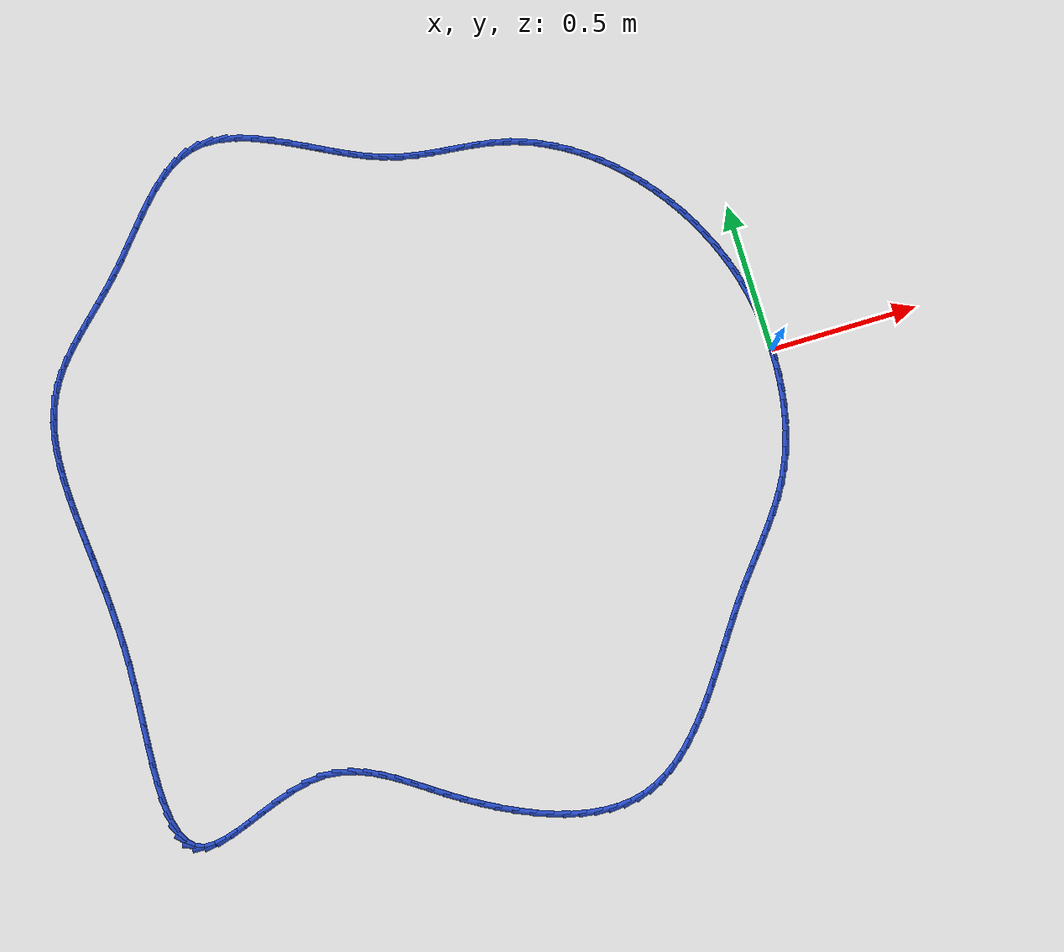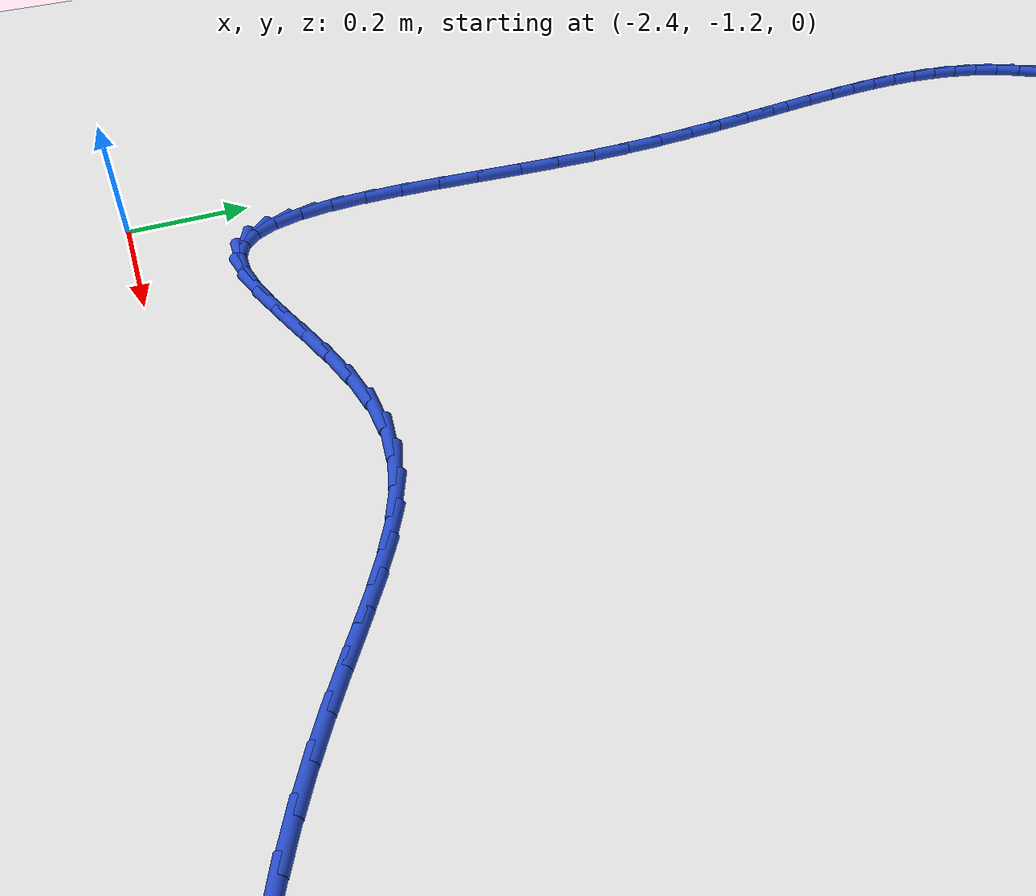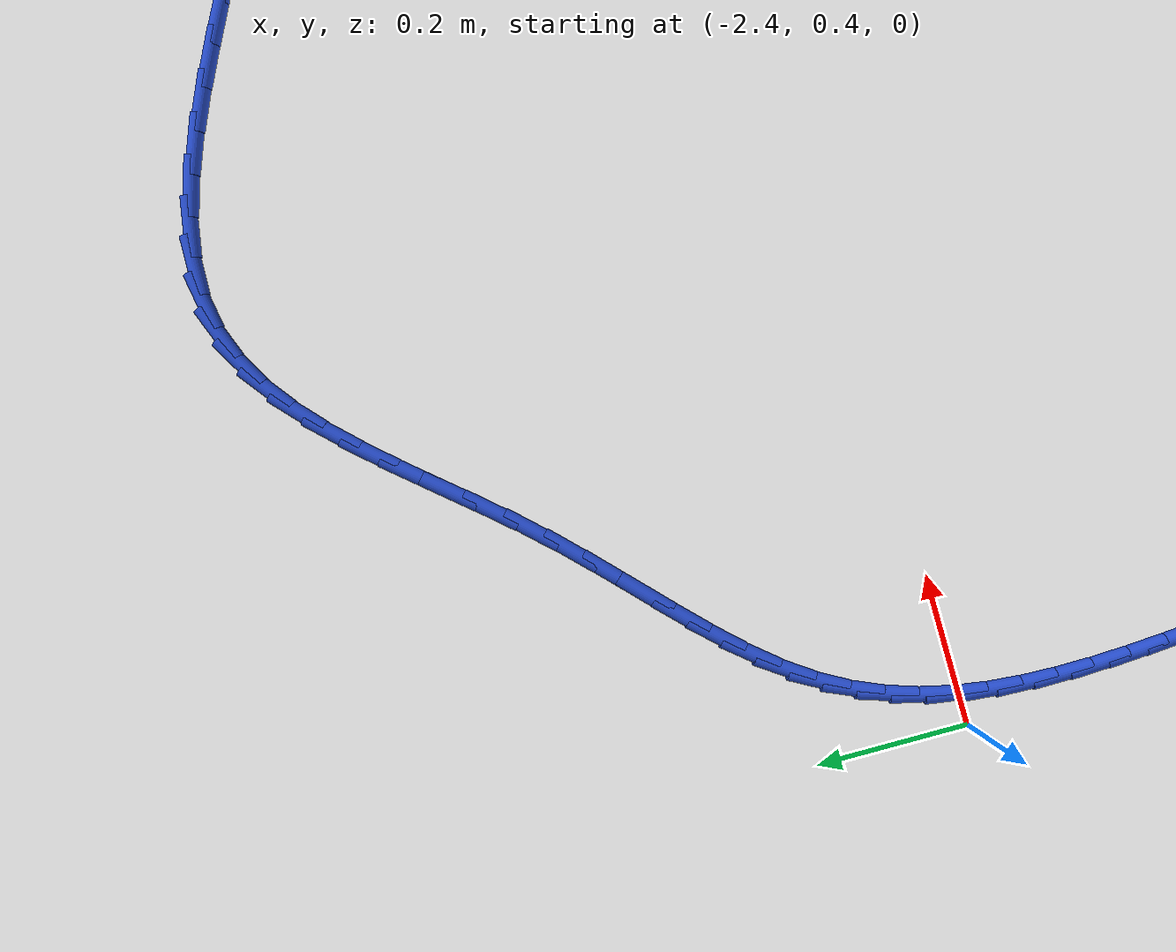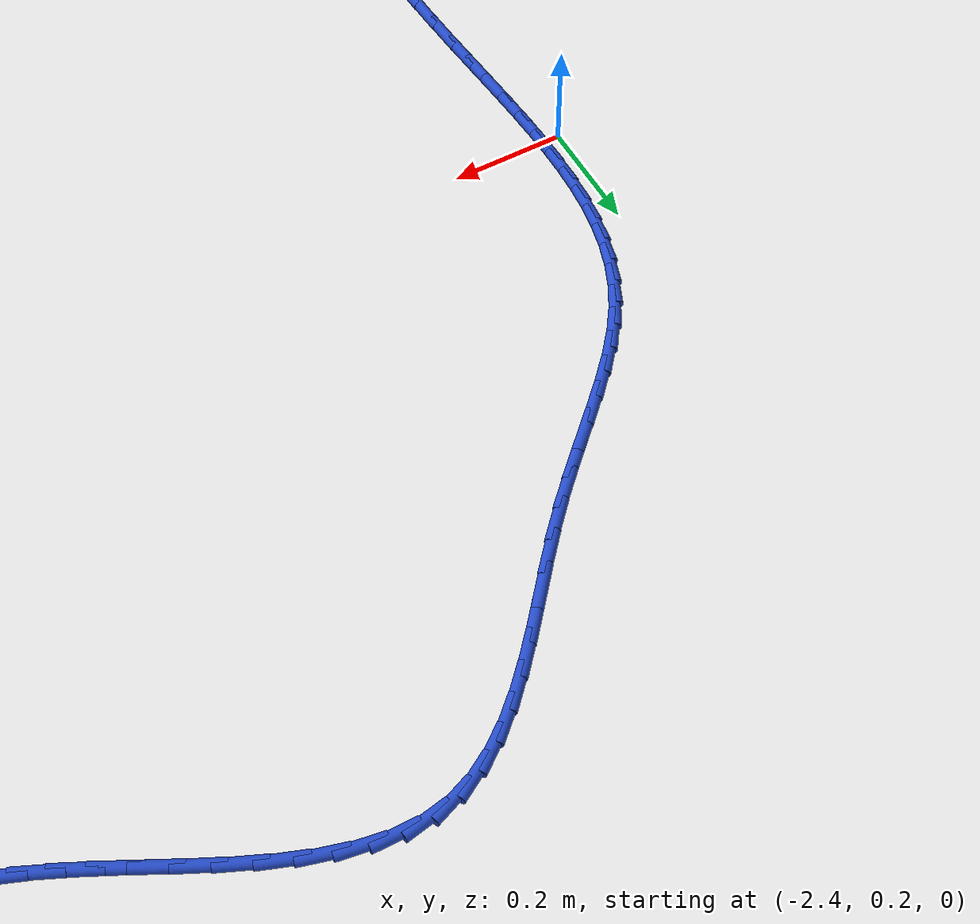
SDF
<sdf version="1.6">
 <world name="default">
  <light name="sun" type="directional">
   <pose>0 0 10 0 -0 0</pose>
   <diffuse>0.8 0.8 0.8 1</diffuse>
   <specular>0.2 0.2 0.2 1</specular>
   <attenuation>
    <range>1000</range>
    <constant>0.9</constant>
    <linear>0.01</linear>
    <quadratic>0.001</quadratic>
   </attenuation>
   <direction>-0.5 0.1 -0.9</direction>
  </light>
  <model name="ground_plane">
   <static>1</static>
   <link name="link">
    <collision name="collision">
     <geometry><plane><normal>0 0 1</normal><size>100 100</size></plane></geometry>
     <surface><friction><ode><mu>100</mu><mu2>50</mu2></ode></friction></surface>
    </collision>
    <visual name="visual">
     <cast_shadows>0</cast_shadows>
     <geometry><plane><normal>0 0 1</normal><size>100 100</size></plane></geometry>
     <material>
      <script><uri>file://media/materials/scripts/gazebo.material</uri><name>Gazebo/WhiteGlow</name></script>
     </material>
    </visual>
   </link>
  </model>
  <gravity>0 0 -9.8</gravity>
  <magnetic_field>6e-06 2.3e-05 -4.2e-05</magnetic_field>
  <atmosphere type="adiabatic"/>
  <physics name="default_physics" default="0" type="ode">
   <max_step_size>0.001</max_step_size>
   <real_time_factor>1</real_time_factor>
   <real_time_update_rate>1000</real_time_update_rate>
  </physics>
  <scene><ambient>0.4 0.4 0.4 1</ambient><background>0.7 0.7 0.7 1</background><shadows>1</shadows></scene>
  <spherical_coordinates>
   <surface_model>EARTH_WGS84</surface_model>
   <latitude_deg>0</latitude_deg>
   <longitude_deg>0</longitude_deg>
   <elevation>0</elevation>
   <heading_deg>0</heading_deg>
  </spherical_coordinates>
  <model name="line">
   <link name="link_0">
    <pose>4.683753385137379e-17 -9.71445146547012e-17 0.01 0 1.57 -1.5415466141234229</pose>
    <collision name="collision">
     <geometry><cylinder><radius>0.01</radius><length>0.08</length></cylinder></geometry>
    </collision>
    <visual name="visual">
     <material>
      <script><name>Gazebo/Blue</name><uri>file://media/materials/scripts/gazebo.material</uri></script>
     </material>
     <geometry><cylinder><radius>0.01</radius><length>0.08</length></cylinder></geometry>
    </visual>
   </link>
   <link name="link_1">
    <pose>-0.0015380150279130165 0.05256723052702508 0.01 0 1.57 -1.4920785525945508</pose>
    <collision name="collision">
     <geometry><cylinder><radius>0.01</radius><length>0.08</length></cylinder></geometry>
    </collision>
    <visual name="visual">
     <material>
      <script><name>Gazebo/Blue</name><uri>file://media/materials/scripts/gazebo.material</uri></script>
     </material>
     <geometry><cylinder><radius>0.01</radius><length>0.08</length></cylinder></geometry>
    </visual>
   </link>
   <link name="link_2">
    <pose>-0.005651078049573215 0.10471001576973192 0.01 0 1.57 -1.4413954976554058</pose>
    <collision name="collision">
     <geometry><cylinder><radius>0.01</radius><length>0.08</length></cylinder></geometry>
    </collision>
    <visual name="visual">
     <material>
      <script><name>Gazebo/Blue</name><uri>file://media/materials/scripts/gazebo.material</uri></script>
     </material>
     <geometry><cylinder><radius>0.01</radius><length>0.08</length></cylinder></geometry>
    </visual>
   </link>
   <link name="link_3">
    <pose>-0.012376972550586392 0.15639679261851733 0.01 0 1.57 -1.3896657407596729</pose>
    <collision name="collision">
     <geometry><cylinder><radius>0.01</radius><length>0.08</length></cylinder></geometry>
    </collision>
    <visual name="visual">
     <material>
      <script><name>Gazebo/Blue</name><uri>file://media/materials/scripts/gazebo.material</uri></script>
     </material>
     <geometry><cylinder><radius>0.01</radius><length>0.08</length></cylinder></geometry>
    </visual>
   </link>
   <link name="link_4">
    <pose>-0.021753482016558384 0.2075959979637782 0.01 0 1.57 -1.337086301904672</pose>
    <collision name="collision">
     <geometry><cylinder><radius>0.01</radius><length>0.08</length></cylinder></geometry>
    </collision>
    <visual name="visual">
     <material>
      <script><name>Gazebo/Blue</name><uri>file://media/materials/scripts/gazebo.material</uri></script>
     </material>
     <geometry><cylinder><radius>0.01</radius><length>0.08</length></cylinder></geometry>
    </visual>
   </link>
   <link name="link_5">
    <pose>-0.03381838993309504 0.2582760686959115 0.01 0 1.57 -1.283879303797767</pose>
    <collision name="collision">
     <geometry><cylinder><radius>0.01</radius><length>0.08</length></cylinder></geometry>
    </collision>
    <visual name="visual">
     <material>
      <script><name>Gazebo/Blue</name><uri>file://media/materials/scripts/gazebo.material</uri></script>
     </material>
     <geometry><cylinder><radius>0.01</radius><length>0.08</length></cylinder></geometry>
    </visual>
   </link>
   <link name="link_6">
    <pose>-0.048609479785802205 0.3084054417053142 0.01 0 1.57 -1.2302867135892297</pose>
    <collision name="collision">
     <geometry><cylinder><radius>0.01</radius><length>0.08</length></cylinder></geometry>
    </collision>
    <visual name="visual">
     <material>
      <script><name>Gazebo/Blue</name><uri>file://media/materials/scripts/gazebo.material</uri></script>
     </material>
     <geometry><cylinder><radius>0.01</radius><length>0.08</length></cylinder></geometry>
    </visual>
   </link>
   <link name="link_7">
    <pose>-0.06616453506028572 0.3579525538823831 0.01 0 1.57 -1.176563697927617</pose>
    <collision name="collision">
     <geometry><cylinder><radius>0.01</radius><length>0.08</length></cylinder></geometry>
    </collision>
    <visual name="visual">
     <material>
      <script><name>Gazebo/Blue</name><uri>file://media/materials/scripts/gazebo.material</uri></script>
     </material>
     <geometry><cylinder><radius>0.01</radius><length>0.08</length></cylinder></geometry>
    </visual>
   </link>
   <link name="link_8">
    <pose>-0.08652133924139689 0.40688584211648177 0.01 0 1.57 -1.123122845600353</pose>
    <collision name="collision">
     <geometry><cylinder><radius>0.01</radius><length>0.08</length></cylinder></geometry>
    </collision>
    <visual name="visual">
     <material>
      <script><name>Gazebo/Blue</name><uri>file://media/materials/scripts/gazebo.material</uri></script>
     </material>
     <geometry><cylinder><radius>0.01</radius><length>0.08</length></cylinder></geometry>
    </visual>
   </link>
   <link name="link_9">
    <pose>-0.10969133001727463 0.4551376683604355 0.01 0 1.57 -1.0705126214260396</pose>
    <collision name="collision">
     <geometry><cylinder><radius>0.01</radius><length>0.08</length></cylinder></geometry>
    </collision>
    <visual name="visual">
     <material>
      <script><name>Gazebo/Blue</name><uri>file://media/materials/scripts/gazebo.material</uri></script>
     </material>
     <geometry><cylinder><radius>0.01</radius><length>0.08</length></cylinder></geometry>
    </visual>
   </link>
   <link name="link_10">
    <pose>-0.13558152764904877 0.5024974172225608 0.01 0 1.57 -1.0183967133618363</pose>
    <collision name="collision">
     <geometry><cylinder><radius>0.01</radius><length>0.08</length></cylinder></geometry>
    </collision>
    <visual name="visual">
     <material>
      <script><name>Gazebo/Blue</name><uri>file://media/materials/scripts/gazebo.material</uri></script>
     </material>
     <geometry><cylinder><radius>0.01</radius><length>0.08</length></cylinder></geometry>
    </visual>
   </link>
   <link name="link_11">
    <pose>-0.16407308727251932 0.5487190565513388 0.01 0 1.57 -0.9662665491765152</pose>
    <collision name="collision">
     <geometry><cylinder><radius>0.01</radius><length>0.08</length></cylinder></geometry>
    </collision>
    <visual name="visual">
     <material>
      <script><name>Gazebo/Blue</name><uri>file://media/materials/scripts/gazebo.material</uri></script>
     </material>
     <geometry><cylinder><radius>0.01</radius><length>0.08</length></cylinder></geometry>
    </visual>
   </link>
   <link name="link_12">
    <pose>-0.19504716402348624 0.5935565541952508 0.01 0 1.57 -0.9136287551357689</pose>
    <collision name="collision">
     <geometry><cylinder><radius>0.01</radius><length>0.08</length></cylinder></geometry>
    </collision>
    <visual name="visual">
     <material>
      <script><name>Gazebo/Blue</name><uri>file://media/materials/scripts/gazebo.material</uri></script>
     </material>
     <geometry><cylinder><radius>0.01</radius><length>0.08</length></cylinder></geometry>
    </visual>
   </link>
   <link name="link_13">
    <pose>-0.22838491303774947 0.6367638780027775 0.01 0 1.57 -0.8599996142701143</pose>
    <collision name="collision">
     <geometry><cylinder><radius>0.01</radius><length>0.08</length></cylinder></geometry>
    </collision>
    <visual name="visual">
     <material>
      <script><name>Gazebo/Blue</name><uri>file://media/materials/scripts/gazebo.material</uri></script>
     </material>
     <geometry><cylinder><radius>0.01</radius><length>0.08</length></cylinder></geometry>
    </visual>
   </link>
   <link name="link_14">
    <pose>-0.2639674894511089 0.6780949958224001 0.01 0 1.57 -0.8049012894406544</pose>
    <collision name="collision">
     <geometry><cylinder><radius>0.01</radius><length>0.08</length></cylinder></geometry>
    </collision>
    <visual name="visual">
     <material>
      <script><name>Gazebo/Blue</name><uri>file://media/materials/scripts/gazebo.material</uri></script>
     </material>
     <geometry><cylinder><radius>0.01</radius><length>0.08</length></cylinder></geometry>
    </visual>
   </link>
   <link name="link_15">
    <pose>-0.3016760483993647 0.7173038755025997 0.01 0 1.57 -0.7478606063406925</pose>
    <collision name="collision">
     <geometry><cylinder><radius>0.01</radius><length>0.08</length></cylinder></geometry>
    </collision>
    <visual name="visual">
     <material>
      <script><name>Gazebo/Blue</name><uri>file://media/materials/scripts/gazebo.material</uri></script>
     </material>
     <geometry><cylinder><radius>0.01</radius><length>0.08</length></cylinder></geometry>
    </visual>
   </link>
   <link name="link_16">
    <pose>-0.34139174501831676 0.7541444848918575 0.01 0 1.57 -0.6884113948911016</pose>
    <collision name="collision">
     <geometry><cylinder><radius>0.01</radius><length>0.08</length></cylinder></geometry>
    </collision>
    <visual name="visual">
     <material>
      <script><name>Gazebo/Blue</name><uri>file://media/materials/scripts/gazebo.material</uri></script>
     </material>
     <geometry><cylinder><radius>0.01</radius><length>0.08</length></cylinder></geometry>
    </visual>
   </link>
   <link name="link_17">
    <pose>-0.38299573444376483 0.7883707918386542 0.01 0 1.57 -0.6261016402470653</pose>
    <collision name="collision">
     <geometry><cylinder><radius>0.01</radius><length>0.08</length></cylinder></geometry>
    </collision>
    <visual name="visual">
     <material>
      <script><name>Gazebo/Blue</name><uri>file://media/materials/scripts/gazebo.material</uri></script>
     </material>
     <geometry><cylinder><radius>0.01</radius><length>0.08</length></cylinder></geometry>
    </visual>
   </link>
   <link name="link_18">
    <pose>-0.4263691718115091 0.819736764191471 0.01 0 1.57 -0.5605069123011129</pose>
    <collision name="collision">
     <geometry><cylinder><radius>0.01</radius><length>0.08</length></cylinder></geometry>
    </collision>
    <visual name="visual">
     <material>
      <script><name>Gazebo/Blue</name><uri>file://media/materials/scripts/gazebo.material</uri></script>
     </material>
     <geometry><cylinder><radius>0.01</radius><length>0.08</length></cylinder></geometry>
    </visual>
   </link>
   <link name="link_19">
    <pose>-0.4713932122573493 0.8479963697987891 0.01 0 1.57 -0.4912515749986578</pose>
    <collision name="collision">
     <geometry><cylinder><radius>0.01</radius><length>0.08</length></cylinder></geometry>
    </collision>
    <visual name="visual">
     <material>
      <script><name>Gazebo/Blue</name><uri>file://media/materials/scripts/gazebo.material</uri></script>
     </material>
     <geometry><cylinder><radius>0.01</radius><length>0.08</length></cylinder></geometry>
    </visual>
   </link>
   <link name="link_20">
    <pose>-0.5179490109170857 0.8729035765090897 0.01 0 1.57 -0.41803888334708594</pose>
    <collision name="collision">
     <geometry><cylinder><radius>0.01</radius><length>0.08</length></cylinder></geometry>
    </collision>
    <visual name="visual">
     <material>
      <script><name>Gazebo/Blue</name><uri>file://media/materials/scripts/gazebo.material</uri></script>
     </material>
     <geometry><cylinder><radius>0.01</radius><length>0.08</length></cylinder></geometry>
    </visual>
   </link>
   <link name="link_21">
    <pose>-0.5659177229265181 0.8942123521708533 0.01 0 1.57 -0.34068993324473923</pose>
    <collision name="collision">
     <geometry><cylinder><radius>0.01</radius><length>0.08</length></cylinder></geometry>
    </collision>
    <visual name="visual">
     <material>
      <script><name>Gazebo/Blue</name><uri>file://media/materials/scripts/gazebo.material</uri></script>
     </material>
     <geometry><cylinder><radius>0.01</radius><length>0.08</length></cylinder></geometry>
    </visual>
   </link>
   <link name="link_22">
    <pose>-0.6151805034214464 0.9116766646325614 0.01 0 1.57 -0.259647384068537</pose>
    <collision name="collision">
     <geometry><cylinder><radius>0.01</radius><length>0.08</length></cylinder></geometry>
    </collision>
    <visual name="visual">
     <material>
      <script><name>Gazebo/Blue</name><uri>file://media/materials/scripts/gazebo.material</uri></script>
     </material>
     <geometry><cylinder><radius>0.01</radius><length>0.08</length></cylinder></geometry>
    </visual>
   </link>
   <link name="link_23">
    <pose>-0.6656144785606424 0.9250741479006304 0.01 0 1.57 -0.18749152417373546</pose>
    <collision name="collision">
     <geometry><cylinder><radius>0.01</radius><length>0.08</length></cylinder></geometry>
    </collision>
    <visual name="visual">
     <material>
      <script><name>Gazebo/Blue</name><uri>file://media/materials/scripts/gazebo.material</uri></script>
     </material>
     <geometry><cylinder><radius>0.01</radius><length>0.08</length></cylinder></geometry>
    </visual>
   </link>
   <link name="link_24">
    <pose>-0.7169881075798372 0.934820744054466 0.01 0 1.57 -0.13781468755106457</pose>
    <collision name="collision">
     <geometry><cylinder><radius>0.01</radius><length>0.08</length></cylinder></geometry>
    </collision>
    <visual name="visual">
     <material>
      <script><name>Gazebo/Blue</name><uri>file://media/materials/scripts/gazebo.material</uri></script>
     </material>
     <geometry><cylinder><radius>0.01</radius><length>0.08</length></cylinder></geometry>
    </visual>
   </link>
   <link name="link_25">
    <pose>-0.7689514720494542 0.9420277440184932 0.01 0 1.57 -0.110924155736938</pose>
    <collision name="collision">
     <geometry><cylinder><radius>0.01</radius><length>0.08</length></cylinder></geometry>
    </collision>
    <visual name="visual">
     <material>
      <script><name>Gazebo/Blue</name><uri>file://media/materials/scripts/gazebo.material</uri></script>
     </material>
     <geometry><cylinder><radius>0.01</radius><length>0.08</length></cylinder></geometry>
    </visual>
   </link>
   <link name="link_26">
    <pose>-0.8211486779530365 0.9478415392356746 0.01 0 1.57 -0.10649837597077871</pose>
    <collision name="collision">
     <geometry><cylinder><radius>0.01</radius><length>0.08</length></cylinder></geometry>
    </collision>
    <visual name="visual">
     <material>
      <script><name>Gazebo/Blue</name><uri>file://media/materials/scripts/gazebo.material</uri></script>
     </material>
     <geometry><cylinder><radius>0.01</radius><length>0.08</length></cylinder></geometry>
    </visual>
   </link>
   <link name="link_27">
    <pose>-0.8732238312741266 0.953408521148972 0.01 0 1.57 -0.12467765539147815</pose>
    <collision name="collision">
     <geometry><cylinder><radius>0.01</radius><length>0.08</length></cylinder></geometry>
    </collision>
    <visual name="visual">
     <material>
      <script><name>Gazebo/Blue</name><uri>file://media/materials/scripts/gazebo.material</uri></script>
     </material>
     <geometry><cylinder><radius>0.01</radius><length>0.08</length></cylinder></geometry>
    </visual>
   </link>
   <link name="link_28">
    <pose>-0.9248210379962669 0.9598750812013485 0.01 0 1.57 -0.16614458556105718</pose>
    <collision name="collision">
     <geometry><cylinder><radius>0.01</radius><length>0.08</length></cylinder></geometry>
    </collision>
    <visual name="visual">
     <material>
      <script><name>Gazebo/Blue</name><uri>file://media/materials/scripts/gazebo.material</uri></script>
     </material>
     <geometry><cylinder><radius>0.01</radius><length>0.08</length></cylinder></geometry>
    </visual>
   </link>
   <link name="link_29">
    <pose>-0.9755844041030004 0.9683876108357663 0.01 0 1.57 -0.23183757921613832</pose>
    <collision name="collision">
     <geometry><cylinder><radius>0.01</radius><length>0.08</length></cylinder></geometry>
    </collision>
    <visual name="visual">
     <material>
      <script><name>Gazebo/Blue</name><uri>file://media/materials/scripts/gazebo.material</uri></script>
     </material>
     <geometry><cylinder><radius>0.01</radius><length>0.08</length></cylinder></geometry>
    </visual>
   </link>
   <link name="link_30">
    <pose>-1.0251587374879436 0.9800912443837164 0.01 0 1.57 -0.312047706217449</pose>
    <collision name="collision">
     <geometry><cylinder><radius>0.01</radius><length>0.08</length></cylinder></geometry>
    </collision>
    <visual name="visual">
     <material>
      <script><name>Gazebo/Blue</name><uri>file://media/materials/scripts/gazebo.material</uri></script>
     </material>
     <geometry><cylinder><radius>0.01</radius><length>0.08</length></cylinder></geometry>
    </visual>
   </link>
   <link name="link_31">
    <pose>-1.073447172660953 0.9956684566922744 0.01 0 1.57 -0.37983506433896475</pose>
    <collision name="collision">
     <geometry><cylinder><radius>0.01</radius><length>0.08</length></cylinder></geometry>
    </collision>
    <visual name="visual">
     <material>
      <script><name>Gazebo/Blue</name><uri>file://media/materials/scripts/gazebo.material</uri></script>
     </material>
     <geometry><cylinder><radius>0.01</radius><length>0.08</length></cylinder></geometry>
    </visual>
   </link>
   <link name="link_32">
    <pose>-1.1209954835743152 1.0146507640374332 0.01 0 1.57 -0.42965821380719876</pose>
    <collision name="collision">
     <geometry><cylinder><radius>0.01</radius><length>0.08</length></cylinder></geometry>
    </collision>
    <visual name="visual">
     <material>
      <script><name>Gazebo/Blue</name><uri>file://media/materials/scripts/gazebo.material</uri></script>
     </material>
     <geometry><cylinder><radius>0.01</radius><length>0.08</length></cylinder></geometry>
    </visual>
   </link>
   <link name="link_33">
    <pose>-1.168447693986961 1.0363937186170487 0.01 0 1.57 -0.46129631175230285</pose>
    <collision name="collision">
     <geometry><cylinder><radius>0.01</radius><length>0.08</length></cylinder></geometry>
    </collision>
    <visual name="visual">
     <material>
      <script><name>Gazebo/Blue</name><uri>file://media/materials/scripts/gazebo.material</uri></script>
     </material>
     <geometry><cylinder><radius>0.01</radius><length>0.08</length></cylinder></geometry>
    </visual>
   </link>
   <link name="link_34">
    <pose>-1.2164478276578201 1.0602528726289766 0.01 0 1.57 -0.47546455752624156</pose>
    <collision name="collision">
     <geometry><cylinder><radius>0.01</radius><length>0.08</length></cylinder></geometry>
    </collision>
    <visual name="visual">
     <material>
      <script><name>Gazebo/Blue</name><uri>file://media/materials/scripts/gazebo.material</uri></script>
     </material>
     <geometry><cylinder><radius>0.01</radius><length>0.08</length></cylinder></geometry>
    </visual>
   </link>
   <link name="link_35">
    <pose>-1.265585394085164 1.0855518241268671 0.01 0 1.57 -0.4727689873372079</pose>
    <collision name="collision">
     <geometry><cylinder><radius>0.01</radius><length>0.08</length></cylinder></geometry>
    </collision>
    <visual name="visual">
     <material>
      <script><name>Gazebo/Blue</name><uri>file://media/materials/scripts/gazebo.material</uri></script>
     </material>
     <geometry><cylinder><radius>0.01</radius><length>0.08</length></cylinder></geometry>
    </visual>
   </link>
   <link name="link_36">
    <pose>-1.3158144010639805 1.1112416647261616 0.01 0 1.57 -0.4535181067150821</pose>
    <collision name="collision">
     <geometry><cylinder><radius>0.01</radius><length>0.08</length></cylinder></geometry>
    </collision>
    <visual name="visual">
     <material>
      <script><name>Gazebo/Blue</name><uri>file://media/materials/scripts/gazebo.material</uri></script>
     </material>
     <geometry><cylinder><radius>0.01</radius><length>0.08</length></cylinder></geometry>
    </visual>
   </link>
   <link name="link_37">
    <pose>-1.3666780116263972 1.136032664784893 0.01 0 1.57 -0.4168555540847507</pose>
    <collision name="collision">
     <geometry><cylinder><radius>0.01</radius><length>0.08</length></cylinder></geometry>
    </collision>
    <visual name="visual">
     <material>
      <script><name>Gazebo/Blue</name><uri>file://media/materials/scripts/gazebo.material</uri></script>
     </material>
     <geometry><cylinder><radius>0.01</radius><length>0.08</length></cylinder></geometry>
    </visual>
   </link>
   <link name="link_38">
    <pose>-1.4177125033881126 1.1586310586971693 0.01 0 1.57 -0.3602195578214304</pose>
    <collision name="collision">
     <geometry><cylinder><radius>0.01</radius><length>0.08</length></cylinder></geometry>
    </collision>
    <visual name="visual">
     <material>
      <script><name>Gazebo/Blue</name><uri>file://media/materials/scripts/gazebo.material</uri></script>
     </material>
     <geometry><cylinder><radius>0.01</radius><length>0.08</length></cylinder></geometry>
    </visual>
   </link>
   <link name="link_39">
    <pose>-1.4684541539648253 1.1777430808570963 0.01 0 1.57 -0.279232193013129</pose>
    <collision name="collision">
     <geometry><cylinder><radius>0.01</radius><length>0.08</length></cylinder></geometry>
    </collision>
    <visual name="visual">
     <material>
      <script><name>Gazebo/Blue</name><uri>file://media/materials/scripts/gazebo.material</uri></script>
     </material>
     <geometry><cylinder><radius>0.01</radius><length>0.08</length></cylinder></geometry>
    </visual>
   </link>
   <link name="link_40">
    <pose>-1.5184392409722343 1.192074965658782 0.01 0 1.57 -0.16775162427579252</pose>
    <collision name="collision">
     <geometry><cylinder><radius>0.01</radius><length>0.08</length></cylinder></geometry>
    </collision>
    <visual name="visual">
     <material>
      <script><name>Gazebo/Blue</name><uri>file://media/materials/scripts/gazebo.material</uri></script>
     </material>
     <geometry><cylinder><radius>0.01</radius><length>0.08</length></cylinder></geometry>
    </visual>
   </link>
   <link name="link_41">
    <pose>-1.567204042026038 1.2003329474963325 0.01 0 1.57 -0.018908075107396106</pose>
    <collision name="collision">
     <geometry><cylinder><radius>0.01</radius><length>0.08</length></cylinder></geometry>
    </collision>
    <visual name="visual">
     <material>
      <script><name>Gazebo/Blue</name><uri>file://media/materials/scripts/gazebo.material</uri></script>
     </material>
     <geometry><cylinder><radius>0.01</radius><length>0.08</length></cylinder></geometry>
    </visual>
   </link>
   <link name="link_42">
    <pose>-1.6142848347419352 1.2012232607638555 0.01 0 1.57 0.1701212312967609</pose>
    <collision name="collision">
     <geometry><cylinder><radius>0.01</radius><length>0.08</length></cylinder></geometry>
    </collision>
    <visual name="visual">
     <material>
      <script><name>Gazebo/Blue</name><uri>file://media/materials/scripts/gazebo.material</uri></script>
     </material>
     <geometry><cylinder><radius>0.01</radius><length>0.08</length></cylinder></geometry>
    </visual>
   </link>
   <link name="link_43">
    <pose>-1.6592343280527753 1.1935017636128293 0.01 0 1.57 0.3661801967702904</pose>
    <collision name="collision">
     <geometry><cylinder><radius>0.01</radius><length>0.08</length></cylinder></geometry>
    </collision>
    <visual name="visual">
     <material>
      <script><name>Gazebo/Blue</name><uri>file://media/materials/scripts/gazebo.material</uri></script>
     </material>
     <geometry><cylinder><radius>0.01</radius><length>0.08</length></cylinder></geometry>
    </visual>
   </link>
   <link name="link_44">
    <pose>-1.7019957820391942 1.1771038066980417 0.01 0 1.57 0.5293730550373316</pose>
    <collision name="collision">
     <geometry><cylinder><radius>0.01</radius><length>0.08</length></cylinder></geometry>
    </collision>
    <visual name="visual">
     <material>
      <script><name>Gazebo/Blue</name><uri>file://media/materials/scripts/gazebo.material</uri></script>
     </material>
     <geometry><cylinder><radius>0.01</radius><length>0.08</length></cylinder></geometry>
    </visual>
   </link>
   <link name="link_45">
    <pose>-1.742910156682548 1.1531658229246404 0.01 0 1.57 0.6550555817626337</pose>
    <collision name="collision">
     <geometry><cylinder><radius>0.01</radius><length>0.08</length></cylinder></geometry>
    </collision>
    <visual name="visual">
     <material>
      <script><name>Gazebo/Blue</name><uri>file://media/materials/scripts/gazebo.material</uri></script>
     </material>
     <geometry><cylinder><radius>0.01</radius><length>0.08</length></cylinder></geometry>
    </visual>
   </link>
   <link name="link_46">
    <pose>-1.782336273179394 1.122878187349913 0.01 0 1.57 0.7467731136661964</pose>
    <collision name="collision">
     <geometry><cylinder><radius>0.01</radius><length>0.08</length></cylinder></geometry>
    </collision>
    <visual name="visual">
     <material>
      <script><name>Gazebo/Blue</name><uri>file://media/materials/scripts/gazebo.material</uri></script>
     </material>
     <geometry><cylinder><radius>0.01</radius><length>0.08</length></cylinder></geometry>
    </visual>
   </link>
   <link name="link_47">
    <pose>-1.8206329527262906 1.0874312750311477 0.01 0 1.57 0.809953976416097</pose>
    <collision name="collision">
     <geometry><cylinder><radius>0.01</radius><length>0.08</length></cylinder></geometry>
    </collision>
    <visual name="visual">
     <material>
      <script><name>Gazebo/Blue</name><uri>file://media/materials/scripts/gazebo.material</uri></script>
     </material>
     <geometry><cylinder><radius>0.01</radius><length>0.08</length></cylinder></geometry>
    </visual>
   </link>
   <link name="link_48">
    <pose>-1.858159016519796 1.0480154610256318 0.01 0 1.57 0.8493652491550342</pose>
    <collision name="collision">
     <geometry><cylinder><radius>0.01</radius><length>0.08</length></cylinder></geometry>
    </collision>
    <visual name="visual">
     <material>
      <script><name>Gazebo/Blue</name><uri>file://media/materials/scripts/gazebo.material</uri></script>
     </material>
     <geometry><cylinder><radius>0.01</radius><length>0.08</length></cylinder></geometry>
    </visual>
   </link>
   <link name="link_49">
    <pose>-1.8952732857564698 1.005821120390654 0.01 0 1.57 0.8683454732291476</pose>
    <collision name="collision">
     <geometry><cylinder><radius>0.01</radius><length>0.08</length></cylinder></geometry>
    </collision>
    <visual name="visual">
     <material>
      <script><name>Gazebo/Blue</name><uri>file://media/materials/scripts/gazebo.material</uri></script>
     </material>
     <geometry><cylinder><radius>0.01</radius><length>0.08</length></cylinder></geometry>
    </visual>
   </link>
   <link name="link_50">
    <pose>-1.9323345816328694 0.9620386281835008 0.01 0 1.57 0.8687525995645669</pose>
    <collision name="collision">
     <geometry><cylinder><radius>0.01</radius><length>0.08</length></cylinder></geometry>
    </collision>
    <visual name="visual">
     <material>
      <script><name>Gazebo/Blue</name><uri>file://media/materials/scripts/gazebo.material</uri></script>
     </material>
     <geometry><cylinder><radius>0.01</radius><length>0.08</length></cylinder></geometry>
    </visual>
   </link>
   <link name="link_51">
    <pose>-1.9697017253455533 0.9178583594614617 0.01 0 1.57 0.8510845574693076</pose>
    <collision name="collision">
     <geometry><cylinder><radius>0.01</radius><length>0.08</length></cylinder></geometry>
    </collision>
    <visual name="visual">
     <material>
      <script><name>Gazebo/Blue</name><uri>file://media/materials/scripts/gazebo.material</uri></script>
     </material>
     <geometry><cylinder><radius>0.01</radius><length>0.08</length></cylinder></geometry>
    </visual>
   </link>
   <link name="link_52">
    <pose>-2.0077335380910797 0.8744706892818236 0.01 0 1.57 0.8164890846452765</pose>
    <collision name="collision">
     <geometry><cylinder><radius>0.01</radius><length>0.08</length></cylinder></geometry>
    </collision>
    <visual name="visual">
     <material>
      <script><name>Gazebo/Blue</name><uri>file://media/materials/scripts/gazebo.material</uri></script>
     </material>
     <geometry><cylinder><radius>0.01</radius><length>0.08</length></cylinder></geometry>
    </visual>
   </link>
   <link name="link_53">
    <pose>-2.0467259559552557 0.8329750158716591 0.01 0 1.57 0.7843755853639921</pose>
    <collision name="collision">
     <geometry><cylinder><radius>0.01</radius><length>0.08</length></cylinder></geometry>
    </collision>
    <visual name="visual">
     <material>
      <script><name>Gazebo/Blue</name><uri>file://media/materials/scripts/gazebo.material</uri></script>
     </material>
     <geometry><cylinder><radius>0.01</radius><length>0.08</length></cylinder></geometry>
    </visual>
   </link>
   <link name="link_54">
    <pose>-2.0862948853971854 0.7934869284267664 0.01 0 1.57 0.7675576930944683</pose>
    <collision name="collision">
     <geometry><cylinder><radius>0.01</radius><length>0.08</length></cylinder></geometry>
    </collision>
    <visual name="visual">
     <material>
      <script><name>Gazebo/Blue</name><uri>file://media/materials/scripts/gazebo.material</uri></script>
     </material>
     <geometry><cylinder><radius>0.01</radius><length>0.08</length></cylinder></geometry>
    </visual>
   </link>
   <link name="link_55">
    <pose>-2.125640570467786 0.7555206711204957 0.01 0 1.57 0.7670903801759016</pose>
    <collision name="collision">
     <geometry><cylinder><radius>0.01</radius><length>0.08</length></cylinder></geometry>
    </collision>
    <visual name="visual">
     <material>
      <script><name>Gazebo/Blue</name><uri>file://media/materials/scripts/gazebo.material</uri></script>
     </material>
     <geometry><cylinder><radius>0.01</radius><length>0.08</length></cylinder></geometry>
    </visual>
   </link>
   <link name="link_56">
    <pose>-2.1639572938121296 0.7185818636712041 0.01 0 1.57 0.7843512614463876</pose>
    <collision name="collision">
     <geometry><cylinder><radius>0.01</radius><length>0.08</length></cylinder></geometry>
    </collision>
    <visual name="visual">
     <material>
      <script><name>Gazebo/Blue</name><uri>file://media/materials/scripts/gazebo.material</uri></script>
     </material>
     <geometry><cylinder><radius>0.01</radius><length>0.08</length></cylinder></geometry>
    </visual>
   </link>
   <link name="link_57">
    <pose>-2.2004393380752885 0.6821761257972505 0.01 0 1.57 0.8213525761232271</pose>
    <collision name="collision">
     <geometry><cylinder><radius>0.01</radius><length>0.08</length></cylinder></geometry>
    </collision>
    <visual name="visual">
     <material>
      <script><name>Gazebo/Blue</name><uri>file://media/materials/scripts/gazebo.material</uri></script>
     </material>
     <geometry><cylinder><radius>0.01</radius><length>0.08</length></cylinder></geometry>
    </visual>
   </link>
   <link name="link_58">
    <pose>-2.234280985902337 0.645809077216992 0.01 0 1.57 0.880725294211941</pose>
    <collision name="collision">
     <geometry><cylinder><radius>0.01</radius><length>0.08</length></cylinder></geometry>
    </collision>
    <visual name="visual">
     <material>
      <script><name>Gazebo/Blue</name><uri>file://media/materials/scripts/gazebo.material</uri></script>
     </material>
     <geometry><cylinder><radius>0.01</radius><length>0.08</length></cylinder></geometry>
    </visual>
   </link>
   <link name="link_59">
    <pose>-2.2646765199383476 0.6089863376487875 0.01 0 1.57 0.9651259260950774</pose>
    <collision name="collision">
     <geometry><cylinder><radius>0.01</radius><length>0.08</length></cylinder></geometry>
    </collision>
    <visual name="visual">
     <material>
      <script><name>Gazebo/Blue</name><uri>file://media/materials/scripts/gazebo.material</uri></script>
     </material>
     <geometry><cylinder><radius>0.01</radius><length>0.08</length></cylinder></geometry>
    </visual>
   </link>
   <link name="link_60">
    <pose>-2.290831020764267 0.5712177623625896 0.01 0 1.57 1.0654334734665476</pose>
    <collision name="collision">
     <geometry><cylinder><radius>0.01</radius><length>0.08</length></cylinder></geometry>
    </collision>
    <visual name="visual">
     <material>
      <script><name>Gazebo/Blue</name><uri>file://media/materials/scripts/gazebo.material</uri></script>
     </material>
     <geometry><cylinder><radius>0.01</radius><length>0.08</length></cylinder></geometry>
    </visual>
   </link>
   <link name="link_61">
    <pose>-2.3124202223223214 0.5321978230789552 0.01 0 1.57 1.1646446879283325</pose>
    <collision name="collision">
     <geometry><cylinder><radius>0.01</radius><length>0.08</length></cylinder></geometry>
    </collision>
    <visual name="visual">
     <material>
      <script><name>Gazebo/Blue</name><uri>file://media/materials/scripts/gazebo.material</uri></script>
     </material>
     <geometry><cylinder><radius>0.01</radius><length>0.08</length></cylinder></geometry>
    </visual>
   </link>
   <link name="link_62">
    <pose>-2.329762436493547 0.49187304635977436 0.01 0 1.57 1.2583311708363665</pose>
    <collision name="collision">
     <geometry><cylinder><radius>0.01</radius><length>0.08</length></cylinder></geometry>
    </collision>
    <visual name="visual">
     <material>
      <script><name>Gazebo/Blue</name><uri>file://media/materials/scripts/gazebo.material</uri></script>
     </material>
     <geometry><cylinder><radius>0.01</radius><length>0.08</length></cylinder></geometry>
    </visual>
   </link>
   <link name="link_63">
    <pose>-2.343222206417527 0.45020809324033517 0.01 0 1.57 1.3437889629129738</pose>
    <collision name="collision">
     <geometry><cylinder><radius>0.01</radius><length>0.08</length></cylinder></geometry>
    </collision>
    <visual name="visual">
     <material>
      <script><name>Gazebo/Blue</name><uri>file://media/materials/scripts/gazebo.material</uri></script>
     </material>
     <geometry><cylinder><radius>0.01</radius><length>0.08</length></cylinder></geometry>
    </visual>
   </link>
   <link name="link_64">
    <pose>-2.3531640752338396 0.4071676247559247 0.01 0 1.57 1.419249392026891</pose>
    <collision name="collision">
     <geometry><cylinder><radius>0.01</radius><length>0.08</length></cylinder></geometry>
    </collision>
    <visual name="visual">
     <material>
      <script><name>Gazebo/Blue</name><uri>file://media/materials/scripts/gazebo.material</uri></script>
     </material>
     <geometry><cylinder><radius>0.01</radius><length>0.08</length></cylinder></geometry>
    </visual>
   </link>
   <link name="link_65">
    <pose>-2.359952586082067 0.3627163019418299 0.01 0 1.57 1.4838718576488055</pose>
    <collision name="collision">
     <geometry><cylinder><radius>0.01</radius><length>0.08</length></cylinder></geometry>
    </collision>
    <visual name="visual">
     <material>
      <script><name>Gazebo/Blue</name><uri>file://media/materials/scripts/gazebo.material</uri></script>
     </material>
     <geometry><cylinder><radius>0.01</radius><length>0.08</length></cylinder></geometry>
    </visual>
   </link>
   <link name="link_66">
    <pose>-2.3639522821017898 0.31681878583333817 0.01 0 1.57 1.5375570756714296</pose>
    <collision name="collision">
     <geometry><cylinder><radius>0.01</radius><length>0.08</length></cylinder></geometry>
    </collision>
    <visual name="visual">
     <material>
      <script><name>Gazebo/Blue</name><uri>file://media/materials/scripts/gazebo.material</uri></script>
     </material>
     <geometry><cylinder><radius>0.01</radius><length>0.08</length></cylinder></geometry>
    </visual>
   </link>
   <link name="link_67">
    <pose>-2.365527706432588 0.26943973746573613 0.01 0 1.57 -1.5608918524345827</pose>
    <collision name="collision">
     <geometry><cylinder><radius>0.01</radius><length>0.08</length></cylinder></geometry>
    </collision>
    <visual name="visual">
     <material>
      <script><name>Gazebo/Blue</name><uri>file://media/materials/scripts/gazebo.material</uri></script>
     </material>
     <geometry><cylinder><radius>0.01</radius><length>0.08</length></cylinder></geometry>
    </visual>
   </link>
   <link name="link_68">
    <pose>-2.3650434022140434 0.22054381787431207 0.01 0 1.57 -1.5276205901495357</pose>
    <collision name="collision">
     <geometry><cylinder><radius>0.01</radius><length>0.08</length></cylinder></geometry>
    </collision>
    <visual name="visual">
     <material>
      <script><name>Gazebo/Blue</name><uri>file://media/materials/scripts/gazebo.material</uri></script>
     </material>
     <geometry><cylinder><radius>0.01</radius><length>0.08</length></cylinder></geometry>
    </visual>
   </link>
   <link name="link_69">
    <pose>-2.3628639125857345 0.17009568809435252 0.01 0 1.57 -1.5034421122580877</pose>
    <collision name="collision">
     <geometry><cylinder><radius>0.01</radius><length>0.08</length></cylinder></geometry>
    </collision>
    <visual name="visual">
     <material>
      <script><name>Gazebo/Blue</name><uri>file://media/materials/scripts/gazebo.material</uri></script>
     </material>
     <geometry><cylinder><radius>0.01</radius><length>0.08</length></cylinder></geometry>
    </visual>
   </link>
   <link name="link_70">
    <pose>-2.3593537806872447 0.11806000916114494 0.01 0 1.57 -1.4875684090410868</pose>
    <collision name="collision">
     <geometry><cylinder><radius>0.01</radius><length>0.08</length></cylinder></geometry>
    </collision>
    <visual name="visual">
     <material>
      <script><name>Gazebo/Blue</name><uri>file://media/materials/scripts/gazebo.material</uri></script>
     </material>
     <geometry><cylinder><radius>0.01</radius><length>0.08</length></cylinder></geometry>
    </visual>
   </link>
   <link name="link_71">
    <pose>-2.354877549658153 0.06440144210997595 0.01 0 1.57 -1.4792581868829755</pose>
    <collision name="collision">
     <geometry><cylinder><radius>0.01</radius><length>0.08</length></cylinder></geometry>
    </collision>
    <visual name="visual">
     <material>
      <script><name>Gazebo/Blue</name><uri>file://media/materials/scripts/gazebo.material</uri></script>
     </material>
     <geometry><cylinder><radius>0.01</radius><length>0.08</length></cylinder></geometry>
    </visual>
   </link>
   <link name="link_72">
    <pose>-2.34979976263804 0.009084647976133689 0.01 0 1.57 -1.477839839660909</pose>
    <collision name="collision">
     <geometry><cylinder><radius>0.01</radius><length>0.08</length></cylinder></geometry>
    </collision>
    <visual name="visual">
     <material>
      <script><name>Gazebo/Blue</name><uri>file://media/materials/scripts/gazebo.material</uri></script>
     </material>
     <geometry><cylinder><radius>0.01</radius><length>0.08</length></cylinder></geometry>
    </visual>
   </link>
   <link name="link_73">
    <pose>-2.3444849627664874 -0.047925712205095033 0.01 0 1.57 -1.4827147392802746</pose>
    <collision name="collision">
     <geometry><cylinder><radius>0.01</radius><length>0.08</length></cylinder></geometry>
    </collision>
    <visual name="visual">
     <material>
      <script><name>Gazebo/Blue</name><uri>file://media/materials/scripts/gazebo.material</uri></script>
     </material>
     <geometry><cylinder><radius>0.01</radius><length>0.08</length></cylinder></geometry>
    </visual>
   </link>
   <link name="link_74">
    <pose>-2.3392976931830742 -0.10666497739842304 0.01 0 1.57 -1.4933494946444272</pose>
    <collision name="collision">
     <geometry><cylinder><radius>0.01</radius><length>0.08</length></cylinder></geometry>
    </collision>
    <visual name="visual">
     <material>
      <script><name>Gazebo/Blue</name><uri>file://media/materials/scripts/gazebo.material</uri></script>
     </material>
     <geometry><cylinder><radius>0.01</radius><length>0.08</length></cylinder></geometry>
    </visual>
   </link>
   <link name="link_75">
    <pose>-2.334602497027382 -0.16716848656856312 0.01 0 1.57 -1.5092627261936897</pose>
    <collision name="collision">
     <geometry><cylinder><radius>0.01</radius><length>0.08</length></cylinder></geometry>
    </collision>
    <visual name="visual">
     <material>
      <script><name>Gazebo/Blue</name><uri>file://media/materials/scripts/gazebo.material</uri></script>
     </material>
     <geometry><cylinder><radius>0.01</radius><length>0.08</length></cylinder></geometry>
    </visual>
   </link>
   <link name="link_76">
    <pose>-2.330763917438993 -0.22947157868022855 0.01 0 1.57 -1.530009776665142</pose>
    <collision name="collision">
     <geometry><cylinder><radius>0.01</radius><length>0.08</length></cylinder></geometry>
    </collision>
    <visual name="visual">
     <material>
      <script><name>Gazebo/Blue</name><uri>file://media/materials/scripts/gazebo.material</uri></script>
     </material>
     <geometry><cylinder><radius>0.01</radius><length>0.08</length></cylinder></geometry>
    </visual>
   </link>
   <link name="link_77">
    <pose>-2.3281464975574853 -0.29360959269813164 0.01 0 1.57 -1.5551674827939042</pose>
    <collision name="collision">
     <geometry><cylinder><radius>0.01</radius><length>0.08</length></cylinder></geometry>
    </collision>
    <visual name="visual">
     <material>
      <script><name>Gazebo/Blue</name><uri>file://media/materials/scripts/gazebo.material</uri></script>
     </material>
     <geometry><cylinder><radius>0.01</radius><length>0.08</length></cylinder></geometry>
    </visual>
   </link>
   <link name="link_78">
    <pose>-2.327114780522441 -0.3596178675869841 0.01 0 1.57 1.55745078624713</pose>
    <collision name="collision">
     <geometry><cylinder><radius>0.01</radius><length>0.08</length></cylinder></geometry>
    </collision>
    <visual name="visual">
     <material>
      <script><name>Gazebo/Blue</name><uri>file://media/materials/scripts/gazebo.material</uri></script>
     </material>
     <geometry><cylinder><radius>0.01</radius><length>0.08</length></cylinder></geometry>
    </visual>
   </link>
   <link name="link_79">
    <pose>-2.328021019264337 -0.4275195712757638 0.01 0 1.57 1.5316532512382517</pose>
    <collision name="collision">
     <geometry><cylinder><radius>0.01</radius><length>0.08</length></cylinder></geometry>
    </collision>
    <visual name="visual">
     <material>
      <script><name>Gazebo/Blue</name><uri>file://media/materials/scripts/gazebo.material</uri></script>
     </material>
     <geometry><cylinder><radius>0.01</radius><length>0.08</length></cylinder></geometry>
    </visual>
   </link>
   <link name="link_80">
    <pose>-2.3307366720785 -0.49686173913643933 0.01 0 1.57 1.5167643529252266</pose>
    <collision name="collision">
     <geometry><cylinder><radius>0.01</radius><length>0.08</length></cylinder></geometry>
    </collision>
    <visual name="visual">
     <material>
      <script><name>Gazebo/Blue</name><uri>file://media/materials/scripts/gazebo.material</uri></script>
     </material>
     <geometry><cylinder><radius>0.01</radius><length>0.08</length></cylinder></geometry>
    </visual>
   </link>
   <link name="link_81">
    <pose>-2.33450687948605 -0.5665711619260696 0.01 0 1.57 1.5124554049348993</pose>
    <collision name="collision">
     <geometry><cylinder><radius>0.01</radius><length>0.08</length></cylinder></geometry>
    </collision>
    <visual name="visual">
     <material>
      <script><name>Gazebo/Blue</name><uri>file://media/materials/scripts/gazebo.material</uri></script>
     </material>
     <geometry><cylinder><radius>0.01</radius><length>0.08</length></cylinder></geometry>
    </visual>
   </link>
   <link name="link_82">
    <pose>-2.338534747785223 -0.6355330037683017 0.01 0 1.57 1.518851066210437</pose>
    <collision name="collision">
     <geometry><cylinder><radius>0.01</radius><length>0.08</length></cylinder></geometry>
    </collision>
    <visual name="visual">
     <material>
      <script><name>Gazebo/Blue</name><uri>file://media/materials/scripts/gazebo.material</uri></script>
     </material>
     <geometry><cylinder><radius>0.01</radius><length>0.08</length></cylinder></geometry>
    </visual>
   </link>
   <link name="link_83">
    <pose>-2.342023383274261 -0.7026324287867841 0.01 0 1.57 1.5372400557956143</pose>
    <collision name="collision">
     <geometry><cylinder><radius>0.01</radius><length>0.08</length></cylinder></geometry>
    </collision>
    <visual name="visual">
     <material>
      <script><name>Gazebo/Blue</name><uri>file://media/materials/scripts/gazebo.material</uri></script>
     </material>
     <geometry><cylinder><radius>0.01</radius><length>0.08</length></cylinder></geometry>
    </visual>
   </link>
   <link name="link_84">
    <pose>-2.3441758922513993 -0.7667546011051674 0.01 0 1.57 1.570471676859739</pose>
    <collision name="collision">
     <geometry><cylinder><radius>0.01</radius><length>0.08</length></cylinder></geometry>
    </collision>
    <visual name="visual">
     <material>
      <script><name>Gazebo/Blue</name><uri>file://media/materials/scripts/gazebo.material</uri></script>
     </material>
     <geometry><cylinder><radius>0.01</radius><length>0.08</length></cylinder></geometry>
    </visual>
   </link>
   <link name="link_85">
    <pose>-2.3441953810148783 -0.8267846848470987 0.01 0 1.57 -1.5177586020661384</pose>
    <collision name="collision">
     <geometry><cylinder><radius>0.01</radius><length>0.08</length></cylinder></geometry>
    </collision>
    <visual name="visual">
     <material>
      <script><name>Gazebo/Blue</name><uri>file://media/materials/scripts/gazebo.material</uri></script>
     </material>
     <geometry><cylinder><radius>0.01</radius><length>0.08</length></cylinder></geometry>
    </visual>
   </link>
   <link name="link_86">
    <pose>-2.3412849558629354 -0.8816078441362282 0.01 0 1.57 -1.4347948766053573</pose>
    <collision name="collision">
     <geometry><cylinder><radius>0.01</radius><length>0.08</length></cylinder></geometry>
    </collision>
    <visual name="visual">
     <material>
      <script><name>Gazebo/Blue</name><uri>file://media/materials/scripts/gazebo.material</uri></script>
     </material>
     <geometry><cylinder><radius>0.01</radius><length>0.08</length></cylinder></geometry>
    </visual>
   </link>
   <link name="link_87">
    <pose>-2.3346477230938096 -0.9301092430962045 0.01 0 1.57 -1.3054184264576614</pose>
    <collision name="collision">
     <geometry><cylinder><radius>0.01</radius><length>0.08</length></cylinder></geometry>
    </collision>
    <visual name="visual">
     <material>
      <script><name>Gazebo/Blue</name><uri>file://media/materials/scripts/gazebo.material</uri></script>
     </material>
     <geometry><cylinder><radius>0.01</radius><length>0.08</length></cylinder></geometry>
    </visual>
   </link>
   <link name="link_88">
    <pose>-2.32348678900574 -0.9711740458506755 0.01 0 1.57 -1.1016316950433602</pose>
    <collision name="collision">
     <geometry><cylinder><radius>0.01</radius><length>0.08</length></cylinder></geometry>
    </collision>
    <visual name="visual">
     <material>
      <script><name>Gazebo/Blue</name><uri>file://media/materials/scripts/gazebo.material</uri></script>
     </material>
     <geometry><cylinder><radius>0.01</radius><length>0.08</length></cylinder></geometry>
    </visual>
   </link>
   <link name="link_89">
    <pose>-2.3070052598969633 -1.003687416523291 0.01 0 1.57 -0.7908569883966381</pose>
    <collision name="collision">
     <geometry><cylinder><radius>0.01</radius><length>0.08</length></cylinder></geometry>
    </collision>
    <visual name="visual">
     <material>
      <script><name>Gazebo/Blue</name><uri>file://media/materials/scripts/gazebo.material</uri></script>
     </material>
     <geometry><cylinder><radius>0.01</radius><length>0.08</length></cylinder></geometry>
    </visual>
   </link>
   <link name="link_90">
    <pose>-2.2844062420657187 -1.0265345192376993 0.01 0 1.57 -0.3880994830792183</pose>
    <collision name="collision">
     <geometry><cylinder><radius>0.01</radius><length>0.08</length></cylinder></geometry>
    </collision>
    <visual name="visual">
     <material>
      <script><name>Gazebo/Blue</name><uri>file://media/materials/scripts/gazebo.material</uri></script>
     </material>
     <geometry><cylinder><radius>0.01</radius><length>0.08</length></cylinder></geometry>
    </visual>
   </link>
   <link name="link_91">
    <pose>-2.2548928931723404 -1.038600609432451 0.01 0 1.57 -0.023858899915953167</pose>
    <collision name="collision">
     <geometry><cylinder><radius>0.01</radius><length>0.08</length></cylinder></geometry>
    </collision>
    <visual name="visual">
     <material>
      <script><name>Gazebo/Blue</name><uri>file://media/materials/scripts/gazebo.material</uri></script>
     </material>
     <geometry><cylinder><radius>0.01</radius><length>0.08</length></cylinder></geometry>
    </visual>
   </link>
   <link name="link_92">
    <pose>-2.2180668612019536 -1.0394794048004357 0.01 0 1.57 0.189862802182624</pose>
    <collision name="collision">
     <geometry><cylinder><radius>0.01</radius><length>0.08</length></cylinder></geometry>
    </collision>
    <visual name="visual">
     <material>
      <script><name>Gazebo/Blue</name><uri>file://media/materials/scripts/gazebo.material</uri></script>
     </material>
     <geometry><cylinder><radius>0.01</radius><length>0.08</length></cylinder></geometry>
    </visual>
   </link>
   <link name="link_93">
    <pose>-2.17488930269319 -1.0311816465723187 0.01 0 1.57 0.30027140485685966</pose>
    <collision name="collision">
     <geometry><cylinder><radius>0.01</radius><length>0.08</length></cylinder></geometry>
    </collision>
    <visual name="visual">
     <material>
      <script><name>Gazebo/Blue</name><uri>file://media/materials/scripts/gazebo.material</uri></script>
     </material>
     <geometry><cylinder><radius>0.01</radius><length>0.08</length></cylinder></geometry>
    </visual>
   </link>
   <link name="link_94">
    <pose>-2.126611046134841 -1.0162330737843865 0.01 0 1.57 0.35076825966194974</pose>
    <collision name="collision">
     <geometry><cylinder><radius>0.01</radius><length>0.08</length></cylinder></geometry>
    </collision>
    <visual name="visual">
     <material>
      <script><name>Gazebo/Blue</name><uri>file://media/materials/scripts/gazebo.material</uri></script>
     </material>
     <geometry><cylinder><radius>0.01</radius><length>0.08</length></cylinder></geometry>
    </visual>
   </link>
   <link name="link_95">
    <pose>-2.0744829200156993 -0.9971594254729241 0.01 0 1.57 0.3611762068760858</pose>
    <collision name="collision">
     <geometry><cylinder><radius>0.01</radius><length>0.08</length></cylinder></geometry>
    </collision>
    <visual name="visual">
     <material>
      <script><name>Gazebo/Blue</name><uri>file://media/materials/scripts/gazebo.material</uri></script>
     </material>
     <geometry><cylinder><radius>0.01</radius><length>0.08</length></cylinder></geometry>
    </visual>
   </link>
   <link name="link_96">
    <pose>-2.0197557528245578 -0.9764864406742187 0.01 0 1.57 0.33858314628906944</pose>
    <collision name="collision">
     <geometry><cylinder><radius>0.01</radius><length>0.08</length></cylinder></geometry>
    </collision>
    <visual name="visual">
     <material>
      <script><name>Gazebo/Blue</name><uri>file://media/materials/scripts/gazebo.material</uri></script>
     </material>
     <geometry><cylinder><radius>0.01</radius><length>0.08</length></cylinder></geometry>
    </visual>
   </link>
   <link name="link_97">
    <pose>-1.963680373050208 -0.9567398584245557 0.01 0 1.57 0.2823286744295047</pose>
    <collision name="collision">
     <geometry><cylinder><radius>0.01</radius><length>0.08</length></cylinder></geometry>
    </collision>
    <visual name="visual">
     <material>
      <script><name>Gazebo/Blue</name><uri>file://media/materials/scripts/gazebo.material</uri></script>
     </material>
     <geometry><cylinder><radius>0.01</radius><length>0.08</length></cylinder></geometry>
    </visual>
   </link>
   <link name="link_98">
    <pose>-1.9075076091814436 -0.9404454177602213 0.01 0 1.57 0.18535563415789003</pose>
    <collision name="collision">
     <geometry><cylinder><radius>0.01</radius><length>0.08</length></cylinder></geometry>
    </collision>
    <visual name="visual">
     <material>
      <script><name>Gazebo/Blue</name><uri>file://media/materials/scripts/gazebo.material</uri></script>
     </material>
     <geometry><cylinder><radius>0.01</radius><length>0.08</length></cylinder></geometry>
    </visual>
   </link>
   <link name="link_99">
    <pose>-1.8524882897070545 -0.930128857717501 0.01 0 1.57 0.03767120536752102</pose>
    <collision name="collision">
     <geometry><cylinder><radius>0.01</radius><length>0.08</length></cylinder></geometry>
    </collision>
    <visual name="visual">
     <material>
      <script><name>Gazebo/Blue</name><uri>file://media/materials/scripts/gazebo.material</uri></script>
     </material>
     <geometry><cylinder><radius>0.01</radius><length>0.08</length></cylinder></geometry>
    </visual>
   </link>
   <link name="link_100">
    <pose>-1.79979146486451 -0.9281427652167378 0.01 0 1.57 -0.12991750881663697</pose>
    <collision name="collision">
     <geometry><cylinder><radius>0.01</radius><length>0.08</length></cylinder></geometry>
    </collision>
    <visual name="visual">
     <material>
      <script><name>Gazebo/Blue</name><uri>file://media/materials/scripts/gazebo.material</uri></script>
     </material>
     <geometry><cylinder><radius>0.01</radius><length>0.08</length></cylinder></geometry>
    </visual>
   </link>
   <link name="link_101">
    <pose>-1.749577228643055 -0.9347034267995861 0.01 0 1.57 -0.2801842022449353</pose>
    <collision name="collision">
     <geometry><cylinder><radius>0.01</radius><length>0.08</length></cylinder></geometry>
    </collision>
    <visual name="visual">
     <material>
      <script><name>Gazebo/Blue</name><uri>file://media/materials/scripts/gazebo.material</uri></script>
     </material>
     <geometry><cylinder><radius>0.01</radius><length>0.08</length></cylinder></geometry>
    </visual>
   </link>
   <link name="link_102">
    <pose>-1.7013259467012993 -0.9485879150747873 0.01 0 1.57 -0.4029506564800169</pose>
    <collision name="collision">
     <geometry><cylinder><radius>0.01</radius><length>0.08</length></cylinder></geometry>
    </collision>
    <visual name="visual">
     <material>
      <script><name>Gazebo/Blue</name><uri>file://media/materials/scripts/gazebo.material</uri></script>
     </material>
     <geometry><cylinder><radius>0.01</radius><length>0.08</length></cylinder></geometry>
    </visual>
   </link>
   <link name="link_103">
    <pose>-1.654505289316738 -0.9685464222511327 0.01 0 1.57 -0.4948743058353372</pose>
    <collision name="collision">
     <geometry><cylinder><radius>0.01</radius><length>0.08</length></cylinder></geometry>
    </collision>
    <visual name="visual">
     <material>
      <script><name>Gazebo/Blue</name><uri>file://media/materials/scripts/gazebo.material</uri></script>
     </material>
     <geometry><cylinder><radius>0.01</radius><length>0.08</length></cylinder></geometry>
    </visual>
   </link>
   <link name="link_104">
    <pose>-1.608582926766866 -0.9933291405374126 0.01 0 1.57 -0.5567720808523011</pose>
    <collision name="collision">
     <geometry><cylinder><radius>0.01</radius><length>0.08</length></cylinder></geometry>
    </collision>
    <visual name="visual">
     <material>
      <script><name>Gazebo/Blue</name><uri>file://media/materials/scripts/gazebo.material</uri></script>
     </material>
     <geometry><cylinder><radius>0.01</radius><length>0.08</length></cylinder></geometry>
    </visual>
   </link>
   <link name="link_105">
    <pose>-1.5630265293291774 -1.0216862621424194 0.01 0 1.57 -0.5910229041675557</pose>
    <collision name="collision">
     <geometry><cylinder><radius>0.01</radius><length>0.08</length></cylinder></geometry>
    </collision>
    <visual name="visual">
     <material>
      <script><name>Gazebo/Blue</name><uri>file://media/materials/scripts/gazebo.material</uri></script>
     </material>
     <geometry><cylinder><radius>0.01</radius><length>0.08</length></cylinder></geometry>
    </visual>
   </link>
   <link name="link_106">
    <pose>-1.5173037672811673 -1.0523679792749427 0.01 0 1.57 -0.5999688595193906</pose>
    <collision name="collision">
     <geometry><cylinder><radius>0.01</radius><length>0.08</length></cylinder></geometry>
    </collision>
    <visual name="visual">
     <material>
      <script><name>Gazebo/Blue</name><uri>file://media/materials/scripts/gazebo.material</uri></script>
     </material>
     <geometry><cylinder><radius>0.01</radius><length>0.08</length></cylinder></geometry>
    </visual>
   </link>
   <link name="link_107">
    <pose>-1.4708823109003302 -1.0841244841437756 0.01 0 1.57 -0.5853732621717056</pose>
    <collision name="collision">
     <geometry><cylinder><radius>0.01</radius><length>0.08</length></cylinder></geometry>
    </collision>
    <visual name="visual">
     <material>
      <script><name>Gazebo/Blue</name><uri>file://media/materials/scripts/gazebo.material</uri></script>
     </material>
     <geometry><cylinder><radius>0.01</radius><length>0.08</length></cylinder></geometry>
    </visual>
   </link>
   <link name="link_108">
    <pose>-1.4232336062238962 -1.1157096367020578 0.01 0 1.57 -0.555068356757433</pose>
    <collision name="collision">
     <geometry><cylinder><radius>0.01</radius><length>0.08</length></cylinder></geometry>
    </collision>
    <visual name="visual">
     <material>
      <script><name>Gazebo/Blue</name><uri>file://media/materials/scripts/gazebo.material</uri></script>
     </material>
     <geometry><cylinder><radius>0.01</radius><length>0.08</length></cylinder></geometry>
    </visual>
   </link>
   <link name="link_109">
    <pose>-1.3741232267944927 -1.1461630101293185 0.01 0 1.57 -0.5206408994084673</pose>
    <collision name="collision">
     <geometry><cylinder><radius>0.01</radius><length>0.08</length></cylinder></geometry>
    </collision>
    <visual name="visual">
     <material>
      <script><name>Gazebo/Blue</name><uri>file://media/materials/scripts/gazebo.material</uri></script>
     </material>
     <geometry><cylinder><radius>0.01</radius><length>0.08</length></cylinder></geometry>
    </visual>
   </link>
   <link name="link_110">
    <pose>-1.3238164442809537 -1.1750095805723006 0.01 0 1.57 -0.4824891064251065</pose>
    <collision name="collision">
     <geometry><cylinder><radius>0.01</radius><length>0.08</length></cylinder></geometry>
    </collision>
    <visual name="visual">
     <material>
      <script><name>Gazebo/Blue</name><uri>file://media/materials/scripts/gazebo.material</uri></script>
     </material>
     <geometry><cylinder><radius>0.01</radius><length>0.08</length></cylinder></geometry>
    </visual>
   </link>
   <link name="link_111">
    <pose>-1.2726270761554106 -1.2018214812026191 0.01 0 1.57 -0.43972542987073115</pose>
    <collision name="collision">
     <geometry><cylinder><radius>0.01</radius><length>0.08</length></cylinder></geometry>
    </collision>
    <visual name="visual">
     <material>
      <script><name>Gazebo/Blue</name><uri>file://media/materials/scripts/gazebo.material</uri></script>
     </material>
     <geometry><cylinder><radius>0.01</radius><length>0.08</length></cylinder></geometry>
    </visual>
   </link>
   <link name="link_112">
    <pose>-1.220868939889997 -1.2261708451918882 0.01 0 1.57 -0.39129410480336435</pose>
    <collision name="collision">
     <geometry><cylinder><radius>0.01</radius><length>0.08</length></cylinder></geometry>
    </collision>
    <visual name="visual">
     <material>
      <script><name>Gazebo/Blue</name><uri>file://media/materials/scripts/gazebo.material</uri></script>
     </material>
     <geometry><cylinder><radius>0.01</radius><length>0.08</length></cylinder></geometry>
    </visual>
   </link>
   <link name="link_113">
    <pose>-1.168855852956842 -1.2476298057117243 0.01 0 1.57 -0.3359323795070126</pose>
    <collision name="collision">
     <geometry><cylinder><radius>0.01</radius><length>0.08</length></cylinder></geometry>
    </collision>
    <visual name="visual">
     <material>
      <script><name>Gazebo/Blue</name><uri>file://media/materials/scripts/gazebo.material</uri></script>
     </material>
     <geometry><cylinder><radius>0.01</radius><length>0.08</length></cylinder></geometry>
    </visual>
   </link>
   <link name="link_114">
    <pose>-1.1169016328280794 -1.2657704959337415 0.01 0 1.57 -0.2721406004940904</pose>
    <collision name="collision">
     <geometry><cylinder><radius>0.01</radius><length>0.08</length></cylinder></geometry>
    </collision>
    <visual name="visual">
     <material>
      <script><name>Gazebo/Blue</name><uri>file://media/materials/scripts/gazebo.material</uri></script>
     </material>
     <geometry><cylinder><radius>0.01</radius><length>0.08</length></cylinder></geometry>
    </visual>
   </link>
   <link name="link_115">
    <pose>-1.0653200969758398 -1.2801650490295553 0.01 0 1.57 -0.19818027809229896</pose>
    <collision name="collision">
     <geometry><cylinder><radius>0.01</radius><length>0.08</length></cylinder></geometry>
    </collision>
    <visual name="visual">
     <material>
      <script><name>Gazebo/Blue</name><uri>file://media/materials/scripts/gazebo.material</uri></script>
     </material>
     <geometry><cylinder><radius>0.01</radius><length>0.08</length></cylinder></geometry>
    </visual>
   </link>
   <link name="link_116">
    <pose>-1.014425062872255 -1.2903855981707806 0.01 0 1.57 -0.11213826941049357</pose>
    <collision name="collision">
     <geometry><cylinder><radius>0.01</radius><length>0.08</length></cylinder></geometry>
    </collision>
    <visual name="visual">
     <material>
      <script><name>Gazebo/Blue</name><uri>file://media/materials/scripts/gazebo.material</uri></script>
     </material>
     <geometry><cylinder><radius>0.01</radius><length>0.08</length></cylinder></geometry>
    </visual>
   </link>
   <link name="link_117">
    <pose>-0.9645303479894584 -1.2960042765290325 0.01 0 1.57 -0.012122373176565693</pose>
    <collision name="collision">
     <geometry><cylinder><radius>0.01</radius><length>0.08</length></cylinder></geometry>
    </collision>
    <visual name="visual">
     <material>
      <script><name>Gazebo/Blue</name><uri>file://media/materials/scripts/gazebo.material</uri></script>
     </material>
     <geometry><cylinder><radius>0.01</radius><length>0.08</length></cylinder></geometry>
    </visual>
   </link>
   <link name="link_118">
    <pose>-0.9159497697995796 -1.2965932172759262 0.01 0 1.57 0.10332384601635607</pose>
    <collision name="collision">
     <geometry><cylinder><radius>0.01</radius><length>0.08</length></cylinder></geometry>
    </collision>
    <visual name="visual">
     <material>
      <script><name>Gazebo/Blue</name><uri>file://media/materials/scripts/gazebo.material</uri></script>
     </material>
     <geometry><cylinder><radius>0.01</radius><length>0.08</length></cylinder></geometry>
    </visual>
   </link>
   <link name="link_119">
    <pose>-0.8689971457747522 -1.2917245535830766 0.01 0 1.57 0.23452084588991967</pose>
    <collision name="collision">
     <geometry><cylinder><radius>0.01</radius><length>0.08</length></cylinder></geometry>
    </collision>
    <visual name="visual">
     <material>
      <script><name>Gazebo/Blue</name><uri>file://media/materials/scripts/gazebo.material</uri></script>
     </material>
     <geometry><cylinder><radius>0.01</radius><length>0.08</length></cylinder></geometry>
    </visual>
   </link>
   <link name="link_120">
    <pose>-0.8239861691867464 -1.2809706597528319 0.01 0 1.57 0.3742038453920018</pose>
    <collision name="collision">
     <geometry><cylinder><radius>0.01</radius><length>0.08</length></cylinder></geometry>
    </collision>
    <visual name="visual">
     <material>
      <script><name>Gazebo/Blue</name><uri>file://media/materials/scripts/gazebo.material</uri></script>
     </material>
     <geometry><cylinder><radius>0.01</radius><length>0.08</length></cylinder></geometry>
    </visual>
   </link>
   <link name="link_121">
    <pose>-0.7811121628452183 -1.2641337222740756 0.01 0 1.57 0.5023926541550996</pose>
    <collision name="collision">
     <geometry><cylinder><radius>0.01</radius><length>0.08</length></cylinder></geometry>
    </collision>
    <visual name="visual">
     <material>
      <script><name>Gazebo/Blue</name><uri>file://media/materials/scripts/gazebo.material</uri></script>
     </material>
     <geometry><cylinder><radius>0.01</radius><length>0.08</length></cylinder></geometry>
    </visual>
   </link>
   <link name="link_122">
    <pose>-0.7402317585320182 -1.2416734846331778 0.01 0 1.57 0.6131886389215405</pose>
    <collision name="collision">
     <geometry><cylinder><radius>0.01</radius><length>0.08</length></cylinder></geometry>
    </collision>
    <visual name="visual">
     <material>
      <script><name>Gazebo/Blue</name><uri>file://media/materials/scripts/gazebo.material</uri></script>
     </material>
     <geometry><cylinder><radius>0.01</radius><length>0.08</length></cylinder></geometry>
    </visual>
   </link>
   <link name="link_123">
    <pose>-0.7011413981891684 -1.2141665468231888 0.01 0 1.57 0.7060206256618373</pose>
    <collision name="collision">
     <geometry><cylinder><radius>0.01</radius><length>0.08</length></cylinder></geometry>
    </collision>
    <visual name="visual">
     <material>
      <script><name>Gazebo/Blue</name><uri>file://media/materials/scripts/gazebo.material</uri></script>
     </material>
     <geometry><cylinder><radius>0.01</radius><length>0.08</length></cylinder></geometry>
    </visual>
   </link>
   <link name="link_124">
    <pose>-0.663637523758694 -1.1821895088371615 0.01 0 1.57 0.7819198715120804</pose>
    <collision name="collision">
     <geometry><cylinder><radius>0.01</radius><length>0.08</length></cylinder></geometry>
    </collision>
    <visual name="visual">
     <material>
      <script><name>Gazebo/Blue</name><uri>file://media/materials/scripts/gazebo.material</uri></script>
     </material>
     <geometry><cylinder><radius>0.01</radius><length>0.08</length></cylinder></geometry>
    </visual>
   </link>
   <link name="link_125">
    <pose>-0.6275165771826201 -1.1463189706681494 0.01 0 1.57 0.8426123011740023</pose>
    <collision name="collision">
     <geometry><cylinder><radius>0.01</radius><length>0.08</length></cylinder></geometry>
    </collision>
    <visual name="visual">
     <material>
      <script><name>Gazebo/Blue</name><uri>file://media/materials/scripts/gazebo.material</uri></script>
     </material>
     <geometry><cylinder><radius>0.01</radius><length>0.08</length></cylinder></geometry>
    </visual>
   </link>
   <link name="link_126">
    <pose>-0.5925750004029693 -1.107131532309203 0.01 0 1.57 0.8899256198481532</pose>
    <collision name="collision">
     <geometry><cylinder><radius>0.01</radius><length>0.08</length></cylinder></geometry>
    </collision>
    <visual name="visual">
     <material>
      <script><name>Gazebo/Blue</name><uri>file://media/materials/scripts/gazebo.material</uri></script>
     </material>
     <geometry><cylinder><radius>0.01</radius><length>0.08</length></cylinder></geometry>
    </visual>
   </link>
   <link name="link_127">
    <pose>-0.5586092353617673 -1.065203793753376 0.01 0 1.57 0.9254842546462393</pose>
    <collision name="collision">
     <geometry><cylinder><radius>0.01</radius><length>0.08</length></cylinder></geometry>
    </collision>
    <visual name="visual">
     <material>
      <script><name>Gazebo/Blue</name><uri>file://media/materials/scripts/gazebo.material</uri></script>
     </material>
     <geometry><cylinder><radius>0.01</radius><length>0.08</length></cylinder></geometry>
    </visual>
   </link>
   <link name="link_128">
    <pose>-0.5254157240010369 -1.021112354993719 0.01 0 1.57 0.9505861568455776</pose>
    <collision name="collision">
     <geometry><cylinder><radius>0.01</radius><length>0.08</length></cylinder></geometry>
    </collision>
    <visual name="visual">
     <material>
      <script><name>Gazebo/Blue</name><uri>file://media/materials/scripts/gazebo.material</uri></script>
     </material>
     <geometry><cylinder><radius>0.01</radius><length>0.08</length></cylinder></geometry>
    </visual>
   </link>
   <link name="link_129">
    <pose>-0.49279090826280325 -0.9754338160232856 0.01 0 1.57 0.966171691227835</pose>
    <collision name="collision">
     <geometry><cylinder><radius>0.01</radius><length>0.08</length></cylinder></geometry>
    </collision>
    <visual name="visual">
     <material>
      <script><name>Gazebo/Blue</name><uri>file://media/materials/scripts/gazebo.material</uri></script>
     </material>
     <geometry><cylinder><radius>0.01</radius><length>0.08</length></cylinder></geometry>
    </visual>
   </link>
   <link name="link_130">
    <pose>-0.4605312300890908 -0.9287447768351278 0.01 0 1.57 0.9728292389051968</pose>
    <collision name="collision">
     <geometry><cylinder><radius>0.01</radius><length>0.08</length></cylinder></geometry>
    </collision>
    <visual name="visual">
     <material>
      <script><name>Gazebo/Blue</name><uri>file://media/materials/scripts/gazebo.material</uri></script>
     </material>
     <geometry><cylinder><radius>0.01</radius><length>0.08</length></cylinder></geometry>
    </visual>
   </link>
   <link name="link_131">
    <pose>-0.4284331314219228 -0.8816218374222969 0.01 0 1.57 0.9708084190905735</pose>
    <collision name="collision">
     <geometry><cylinder><radius>0.01</radius><length>0.08</length></cylinder></geometry>
    </collision>
    <visual name="visual">
     <material>
      <script><name>Gazebo/Blue</name><uri>file://media/materials/scripts/gazebo.material</uri></script>
     </material>
     <geometry><cylinder><radius>0.01</radius><length>0.08</length></cylinder></geometry>
    </visual>
   </link>
   <link name="link_132">
    <pose>-0.39629305420332456 -0.8346415977778469 0.01 0 1.57 0.960027480168616</pose>
    <collision name="collision">
     <geometry><cylinder><radius>0.01</radius><length>0.08</length></cylinder></geometry>
    </collision>
    <visual name="visual">
     <material>
      <script><name>Gazebo/Blue</name><uri>file://media/materials/scripts/gazebo.material</uri></script>
     </material>
     <geometry><cylinder><radius>0.01</radius><length>0.08</length></cylinder></geometry>
    </visual>
   </link>
   <link name="link_133">
    <pose>-0.36390744037531925 -0.7883806578948278 0.01 0 1.57 0.9400701791559314</pose>
    <collision name="collision">
     <geometry><cylinder><radius>0.01</radius><length>0.08</length></cylinder></geometry>
    </collision>
    <visual name="visual">
     <material>
      <script><name>Gazebo/Blue</name><uri>file://media/materials/scripts/gazebo.material</uri></script>
     </material>
     <geometry><cylinder><radius>0.01</radius><length>0.08</length></cylinder></geometry>
    </visual>
   </link>
   <link name="link_134">
    <pose>-0.3310727318799316 -0.7434156177662932 0.01 0 1.57 0.9138038056923773</pose>
    <collision name="collision">
     <geometry><cylinder><radius>0.01</radius><length>0.08</length></cylinder></geometry>
    </collision>
    <visual name="visual">
     <material>
      <script><name>Gazebo/Blue</name><uri>file://media/materials/scripts/gazebo.material</uri></script>
     </material>
     <geometry><cylinder><radius>0.01</radius><length>0.08</length></cylinder></geometry>
    </visual>
   </link>
   <link name="link_135">
    <pose>-0.2976982263226795 -0.7001449965120148 0.01 0 1.57 0.8957266469965603</pose>
    <collision name="collision">
     <geometry><cylinder><radius>0.01</radius><length>0.08</length></cylinder></geometry>
    </collision>
    <visual name="visual">
     <material>
      <script><name>Gazebo/Blue</name><uri>file://media/materials/scripts/gazebo.material</uri></script>
     </material>
     <geometry><cylinder><radius>0.01</radius><length>0.08</length></cylinder></geometry>
    </visual>
   </link>
   <link name="link_136">
    <pose>-0.2641530333069873 -0.6582417517726287 0.01 0 1.57 0.8902660640333042</pose>
    <collision name="collision">
     <geometry><cylinder><radius>0.01</radius><length>0.08</length></cylinder></geometry>
    </collision>
    <visual name="visual">
     <material>
      <script><name>Gazebo/Blue</name><uri>file://media/materials/scripts/gazebo.material</uri></script>
     </material>
     <geometry><cylinder><radius>0.01</radius><length>0.08</length></cylinder></geometry>
    </visual>
   </link>
   <link name="link_137">
    <pose>-0.23092335160231126 -0.617194080049696 0.01 0 1.57 0.898083254927693</pose>
    <collision name="collision">
     <geometry><cylinder><radius>0.01</radius><length>0.08</length></cylinder></geometry>
    </collision>
    <visual name="visual">
     <material>
      <script><name>Gazebo/Blue</name><uri>file://media/materials/scripts/gazebo.material</uri></script>
     </material>
     <geometry><cylinder><radius>0.01</radius><length>0.08</length></cylinder></geometry>
    </visual>
   </link>
   <link name="link_138">
    <pose>-0.19849538000468836 -0.5764901778028334 0.01 0 1.57 0.9197267295859819</pose>
    <collision name="collision">
     <geometry><cylinder><radius>0.01</radius><length>0.08</length></cylinder></geometry>
    </collision>
    <visual name="visual">
     <material>
      <script><name>Gazebo/Blue</name><uri>file://media/materials/scripts/gazebo.material</uri></script>
     </material>
     <geometry><cylinder><radius>0.01</radius><length>0.08</length></cylinder></geometry>
    </visual>
   </link>
   <link name="link_139">
    <pose>-0.1673553173101543 -0.535618241491656 0.01 0 1.57 0.955566729660614</pose>
    <collision name="collision">
     <geometry><cylinder><radius>0.01</radius><length>0.08</length></cylinder></geometry>
    </collision>
    <visual name="visual">
     <material>
      <script><name>Gazebo/Blue</name><uri>file://media/materials/scripts/gazebo.material</uri></script>
     </material>
     <geometry><cylinder><radius>0.01</radius><length>0.08</length></cylinder></geometry>
    </visual>
   </link>
   <link name="link_140">
    <pose>-0.13798936231474668 -0.49406646757578154 0.01 0 1.57 1.0056457485435535</pose>
    <collision name="collision">
     <geometry><cylinder><radius>0.01</radius><length>0.08</length></cylinder></geometry>
    </collision>
    <visual name="visual">
     <material>
      <script><name>Gazebo/Blue</name><uri>file://media/materials/scripts/gazebo.material</uri></script>
     </material>
     <geometry><cylinder><radius>0.01</radius><length>0.08</length></cylinder></geometry>
    </visual>
   </link>
   <link name="link_141">
    <pose>-0.11088371381450104 -0.4513230525148244 0.01 0 1.57 1.0694507475120054</pose>
    <collision name="collision">
     <geometry><cylinder><radius>0.01</radius><length>0.08</length></cylinder></geometry>
    </collision>
    <visual name="visual">
     <material>
      <script><name>Gazebo/Blue</name><uri>file://media/materials/scripts/gazebo.material</uri></script>
     </material>
     <geometry><cylinder><radius>0.01</radius><length>0.08</length></cylinder></geometry>
    </visual>
   </link>
   <link name="link_142">
    <pose>-0.08652457060545465 -0.4068761927684022 0.01 0 1.57 1.1428516847063208</pose>
    <collision name="collision">
     <geometry><cylinder><radius>0.01</radius><length>0.08</length></cylinder></geometry>
    </collision>
    <visual name="visual">
     <material>
      <script><name>Gazebo/Blue</name><uri>file://media/materials/scripts/gazebo.material</uri></script>
     </material>
     <geometry><cylinder><radius>0.01</radius><length>0.08</length></cylinder></geometry>
    </visual>
   </link>
   <link name="link_143">
    <pose>-0.06530345044011929 -0.36035249288975907 0.01 0 1.57 1.2135093070897185</pose>
    <collision name="collision">
     <geometry><cylinder><radius>0.01</radius><length>0.08</length></cylinder></geometry>
    </collision>
    <visual name="visual">
     <material>
      <script><name>Gazebo/Blue</name><uri>file://media/materials/scripts/gazebo.material</uri></script>
     </material>
     <geometry><cylinder><radius>0.01</radius><length>0.08</length></cylinder></geometry>
    </visual>
   </link>
   <link name="link_144">
    <pose>-0.047229644005593326 -0.31193731045689066 0.01 0 1.57 1.2789808162319296</pose>
    <collision name="collision">
     <geometry><cylinder><radius>0.01</radius><length>0.08</length></cylinder></geometry>
    </collision>
    <visual name="visual">
     <material>
      <script><name>Gazebo/Blue</name><uri>file://media/materials/scripts/gazebo.material</uri></script>
     </material>
     <geometry><cylinder><radius>0.01</radius><length>0.08</length></cylinder></geometry>
    </visual>
   </link>
   <link name="link_145">
    <pose>-0.03221600141529207 -0.2619569832847579 0.01 0 1.57 1.339907914505477</pose>
    <collision name="collision">
     <geometry><cylinder><radius>0.01</radius><length>0.08</length></cylinder></geometry>
    </collision>
    <visual name="visual">
     <material>
      <script><name>Gazebo/Blue</name><uri>file://media/materials/scripts/gazebo.material</uri></script>
     </material>
     <geometry><cylinder><radius>0.01</radius><length>0.08</length></cylinder></geometry>
    </visual>
   </link>
   <link name="link_146">
    <pose>-0.02017537277986783 -0.21073784919235594 0.01 0 1.57 1.3969600809669587</pose>
    <collision name="collision">
     <geometry><cylinder><radius>0.01</radius><length>0.08</length></cylinder></geometry>
    </collision>
    <visual name="visual">
     <material>
      <script><name>Gazebo/Blue</name><uri>file://media/materials/scripts/gazebo.material</uri></script>
     </material>
     <geometry><cylinder><radius>0.01</radius><length>0.08</length></cylinder></geometry>
    </visual>
   </link>
   <link name="link_147">
    <pose>-0.011020608209973696 -0.15860624599868225 0.01 0 1.57 1.4508079019767648</pose>
    <collision name="collision">
     <geometry><cylinder><radius>0.01</radius><length>0.08</length></cylinder></geometry>
    </collision>
    <visual name="visual">
     <material>
      <script><name>Gazebo/Blue</name><uri>file://media/materials/scripts/gazebo.material</uri></script>
     </material>
     <geometry><cylinder><radius>0.01</radius><length>0.08</length></cylinder></geometry>
    </visual>
   </link>
   <link name="link_148">
    <pose>-0.004664557816262557 -0.10588851152273447 0.01 0 1.57 1.5021114832421587</pose>
    <collision name="collision">
     <geometry><cylinder><radius>0.01</radius><length>0.08</length></cylinder></geometry>
    </collision>
    <visual name="visual">
     <material>
      <script><name>Gazebo/Blue</name><uri>file://media/materials/scripts/gazebo.material</uri></script>
     </material>
     <geometry><cylinder><radius>0.01</radius><length>0.08</length></cylinder></geometry>
    </visual>
   </link>
   <link name="link_149">
    <pose>-0.0010200717093870005 -0.05291098358350759 0.01 0 1.57 1.551519698612185</pose>
    <collision name="collision">
     <geometry><cylinder><radius>0.01</radius><length>0.08</length></cylinder></geometry>
    </collision>
    <visual name="visual">
     <material>
      <script><name>Gazebo/Blue</name><uri>file://media/materials/scripts/gazebo.material</uri></script>
     </material>
     <geometry><cylinder><radius>0.01</radius><length>0.08</length></cylinder></geometry>
    </visual>
   </link>
   <link name="link_150">
    <pose>4.336808689942018e-17 -8.326672684688674e-17 0.01 0 1.57 -1.541915409535821</pose>
    <collision name="collision">
     <geometry><cylinder><radius>0.01</radius><length>0.08</length></cylinder></geometry>
    </collision>
    <visual name="visual">
     <material>
      <script><name>Gazebo/Blue</name><uri>file://media/materials/scripts/gazebo.material</uri></script>
     </material>
     <geometry><cylinder><radius>0.01</radius><length>0.08</length></cylinder></geometry>
    </visual>
   </link>
   <link name="link_151">
    <pose>-0.0015171927987542473 0.05251810140879399 0.01 0 1.57 -1.541915409535821</pose>
    <collision name="collision">
     <geometry><cylinder><radius>0.01</radius><length>0.08</length></cylinder></geometry>
    </collision>
    <visual name="visual">
     <material>
      <script><name>Gazebo/Blue</name><uri>file://media/materials/scripts/gazebo.material</uri></script>
     </material>
     <geometry><cylinder><radius>0.01</radius><length>0.08</length></cylinder></geometry>
    </visual>
   </link>
  </model>
 </world>
</sdf>
